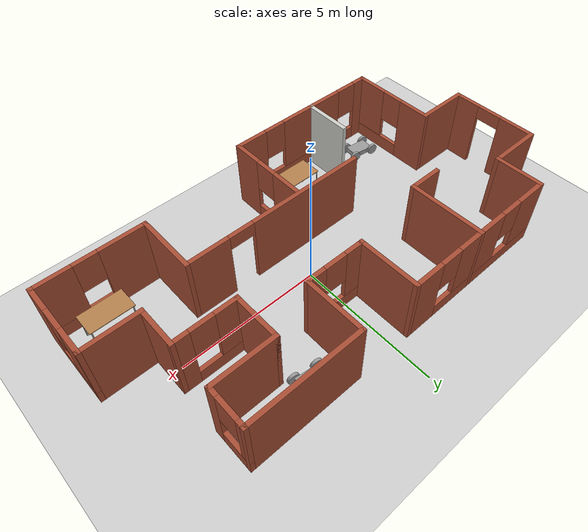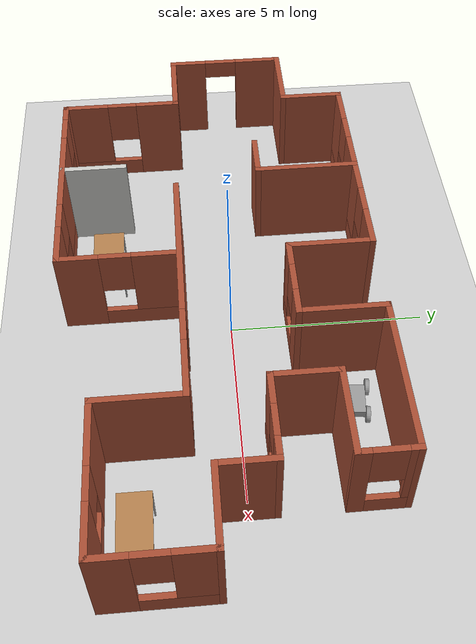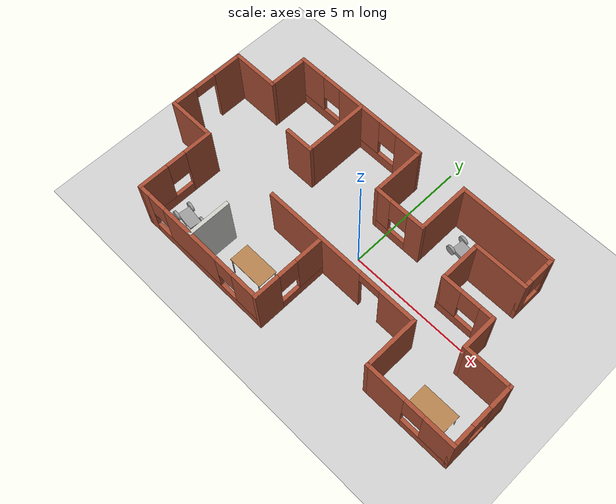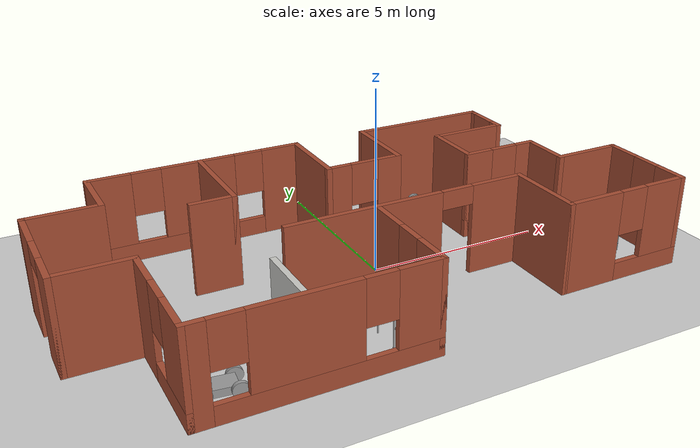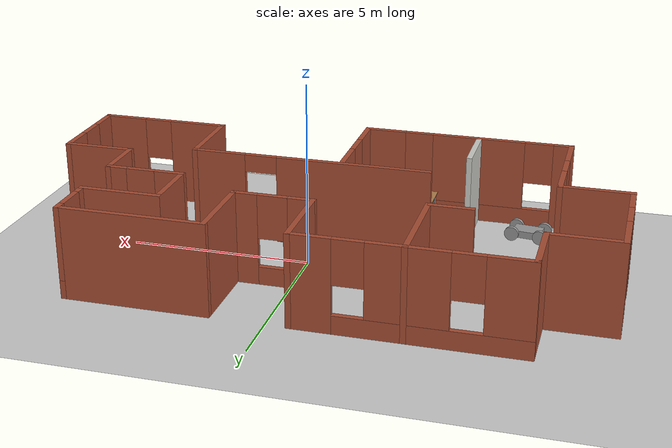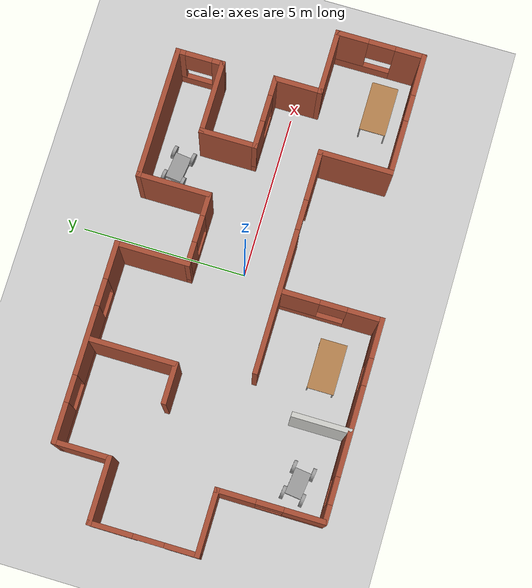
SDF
<sdf version="1.6">
 <world name="default">
  <light name="sun" type="directional">
   <pose>0 0 10 0 -0 0</pose>
   <diffuse>0.8 0.8 0.8 1</diffuse>
   <specular>0.2 0.2 0.2 1</specular>
   <attenuation>
    <range>1000</range>
    <constant>0.9</constant>
    <linear>0.01</linear>
    <quadratic>0.001</quadratic>
   </attenuation>
   <direction>-0.5 0.1 -0.9</direction>
  </light>
  <model name="ground_plane">
   <static>1</static>
   <link name="link">
    <collision name="collision">
     <geometry><plane><normal>0 0 1</normal><size>100 100</size></plane></geometry>
     <surface><friction><ode><mu>100</mu><mu2>50</mu2></ode></friction></surface>
    </collision>
    <visual name="visual">
     <cast_shadows>0</cast_shadows>
     <geometry><plane><normal>0 0 1</normal><size>100 100</size></plane></geometry>
     <material>
      <script><uri>file://media/materials/scripts/gazebo.material</uri><name>Gazebo/Grey</name></script>
     </material>
    </visual>
   </link>
  </model>
  <gravity>0 0 -9.8</gravity>
  <magnetic_field>6e-06 2.3e-05 -4.2e-05</magnetic_field>
  <atmosphere type="adiabatic"/>
  <physics name="default_physics" default="0" type="ode">
   <max_step_size>0.001</max_step_size>
   <real_time_factor>1</real_time_factor>
   <real_time_update_rate>1000</real_time_update_rate>
  </physics>
  <scene><ambient>0.4 0.4 0.4 1</ambient><background>0.7 0.7 0.7 1</background><shadows>1</shadows></scene>
  <spherical_coordinates>
   <surface_model>EARTH_WGS84</surface_model>
   <latitude_deg>0</latitude_deg>
   <longitude_deg>0</longitude_deg>
   <elevation>0</elevation>
   <heading_deg>0</heading_deg>
  </spherical_coordinates>
  <model name="building">
   <pose>-0.550552 -0.291737 0 0 -0 0</pose>
   <link name="Wall_1">
    <pose>0.85 -0.900213 0 0 -0 0</pose>
    <visual name="Wall_1_Visual_0">
     <pose>-1.22383 0 1.25 0 -0 0</pose>
     <geometry><box><size>4.30235 0.15 2.5</size></box></geometry>
     <material>
      <script><uri>file://media/materials/scripts/gazebo.material</uri><name>Gazebo/Bricks</name></script>
      <ambient>0.996078 0.47451 0.0196078 1</ambient>
     </material>
     <meta><layer>0</layer></meta>
    </visual>
    <collision name="Wall_1_Collision_0">
     <geometry><box><size>4.30235 0.15 2.5</size></box></geometry>
     <pose>-1.22383 0 1.25 0 -0 0</pose>
    </collision>
    <visual name="Wall_1_Visual_1">
     <pose>2.60117 0 1.25 0 -0 0</pose>
     <geometry><box><size>1.54765 0.15 2.5</size></box></geometry>
     <material>
      <script><uri>file://media/materials/scripts/gazebo.material</uri><name>Gazebo/Bricks</name></script>
      <ambient>0.996078 0.47451 0.0196078 1</ambient>
     </material>
     <meta><layer>0</layer></meta>
    </visual>
    <collision name="Wall_1_Collision_1">
     <geometry><box><size>1.54765 0.15 2.5</size></box></geometry>
     <pose>2.60117 0 1.25 0 -0 0</pose>
    </collision>
    <visual name="Wall_1_Visual_2">
     <pose>1.37735 0 2.25 0 -0 0</pose>
     <geometry><box><size>0.9 0.15 0.5</size></box></geometry>
     <material>
      <script><uri>file://media/materials/scripts/gazebo.material</uri><name>Gazebo/Bricks</name></script>
      <ambient>0.996078 0.47451 0.0196078 1</ambient>
     </material>
     <meta><layer>0</layer></meta>
    </visual>
    <collision name="Wall_1_Collision_2">
     <geometry><box><size>0.9 0.15 0.5</size></box></geometry>
     <pose>1.37735 0 2.25 0 -0 0</pose>
    </collision>
   </link>
   <link name="Wall_10">
    <pose>5.9 3.22479 0 0 -0 1.5708</pose>
    <visual name="Wall_10_Visual_0">
     <pose>-0.55649 0 1.25 0 -0 0</pose>
     <geometry><box><size>0.38702 0.15 2.5</size></box></geometry>
     <material>
      <script><uri>file://media/materials/scripts/gazebo.material</uri><name>Gazebo/Bricks</name></script>
      <ambient>0.996078 0.47451 0.0196078 1</ambient>
     </material>
     <meta><layer>0</layer></meta>
    </visual>
    <collision name="Wall_10_Collision_0">
     <geometry><box><size>0.38702 0.15 2.5</size></box></geometry>
     <pose>-0.55649 0 1.25 0 -0 0</pose>
    </collision>
    <visual name="Wall_10_Visual_1">
     <pose>0.19351 0 0.25 0 -0 0</pose>
     <geometry><box><size>1.11298 0.15 0.5</size></box></geometry>
     <material>
      <script><uri>file://media/materials/scripts/gazebo.material</uri><name>Gazebo/Bricks</name></script>
      <ambient>0.996078 0.47451 0.0196078 1</ambient>
     </material>
     <meta><layer>0</layer></meta>
    </visual>
    <collision name="Wall_10_Collision_1">
     <geometry><box><size>1.11298 0.15 0.5</size></box></geometry>
     <pose>0.19351 0 0.25 0 -0 0</pose>
    </collision>
    <visual name="Wall_10_Visual_2">
     <pose>0.59351 0 1.5 0 -0 0</pose>
     <geometry><box><size>0.31298 0.15 2</size></box></geometry>
     <material>
      <script><uri>file://media/materials/scripts/gazebo.material</uri><name>Gazebo/Bricks</name></script>
      <ambient>0.996078 0.47451 0.0196078 1</ambient>
     </material>
     <meta><layer>0</layer></meta>
    </visual>
    <collision name="Wall_10_Collision_2">
     <geometry><box><size>0.31298 0.15 2</size></box></geometry>
     <pose>0.59351 0 1.5 0 -0 0</pose>
    </collision>
    <visual name="Wall_10_Visual_3">
     <pose>0.03702 0 1.9 0 -0 0</pose>
     <geometry><box><size>0.8 0.15 1.2</size></box></geometry>
     <material>
      <script><uri>file://media/materials/scripts/gazebo.material</uri><name>Gazebo/Bricks</name></script>
      <ambient>0.996078 0.47451 0.0196078 1</ambient>
     </material>
     <meta><layer>0</layer></meta>
    </visual>
    <collision name="Wall_10_Collision_3">
     <geometry><box><size>0.8 0.15 1.2</size></box></geometry>
     <pose>0.03702 0 1.9 0 -0 0</pose>
    </collision>
   </link>
   <link name="Wall_11">
    <collision name="Wall_11_Collision">
     <geometry><box><size>4 0.15 2.5</size></box></geometry>
     <pose>0 0 1.25 0 -0 0</pose>
    </collision>
    <visual name="Wall_11_Visual">
     <pose>0 0 1.25 0 -0 0</pose>
     <geometry><box><size>4 0.15 2.5</size></box></geometry>
     <material>
      <script><uri>file://media/materials/scripts/gazebo.material</uri><name>Gazebo/Bricks</name></script>
      <ambient>0.996078 0.47451 0.0196078 1</ambient>
     </material>
     <meta><layer>0</layer></meta>
    </visual>
    <pose>3.975 3.89979 0 0 -0 3.14159</pose>
   </link>
   <link name="Wall_12">
    <collision name="Wall_12_Collision">
     <geometry><box><size>2.25 0.15 2.5</size></box></geometry>
     <pose>0 0 1.25 0 -0 0</pose>
    </collision>
    <visual name="Wall_12_Visual">
     <pose>0 0 1.25 0 -0 0</pose>
     <geometry><box><size>2.25 0.15 2.5</size></box></geometry>
     <material>
      <script><uri>file://media/materials/scripts/gazebo.material</uri><name>Gazebo/Bricks</name></script>
      <ambient>0.996078 0.47451 0.0196078 1</ambient>
     </material>
     <meta><layer>0</layer></meta>
    </visual>
    <pose>2.05 2.84979 0 0 0 -1.5708</pose>
   </link>
   <link name="Wall_13">
    <pose>1 1.79979 0 0 -0 3.14159</pose>
    <visual name="Wall_13_Visual_0">
     <pose>-0.76437 0 1.25 0 -0 0</pose>
     <geometry><box><size>0.72126 0.15 2.5</size></box></geometry>
     <material>
      <script><uri>file://media/materials/scripts/gazebo.material</uri><name>Gazebo/Bricks</name></script>
      <ambient>0.996078 0.47451 0.0196078 1</ambient>
     </material>
     <meta><layer>0</layer></meta>
    </visual>
    <collision name="Wall_13_Collision_0">
     <geometry><box><size>0.72126 0.15 2.5</size></box></geometry>
     <pose>-0.76437 0 1.25 0 -0 0</pose>
    </collision>
    <visual name="Wall_13_Visual_1">
     <pose>0.36063 0 0.25 0 -0 0</pose>
     <geometry><box><size>1.52874 0.15 0.5</size></box></geometry>
     <material>
      <script><uri>file://media/materials/scripts/gazebo.material</uri><name>Gazebo/Bricks</name></script>
      <ambient>0.996078 0.47451 0.0196078 1</ambient>
     </material>
     <meta><layer>0</layer></meta>
    </visual>
    <collision name="Wall_13_Collision_1">
     <geometry><box><size>1.52874 0.15 0.5</size></box></geometry>
     <pose>0.36063 0 0.25 0 -0 0</pose>
    </collision>
    <visual name="Wall_13_Visual_2">
     <pose>0.76063 0 1.5 0 -0 0</pose>
     <geometry><box><size>0.72874 0.15 2</size></box></geometry>
     <material>
      <script><uri>file://media/materials/scripts/gazebo.material</uri><name>Gazebo/Bricks</name></script>
      <ambient>0.996078 0.47451 0.0196078 1</ambient>
     </material>
     <meta><layer>0</layer></meta>
    </visual>
    <collision name="Wall_13_Collision_2">
     <geometry><box><size>0.72874 0.15 2</size></box></geometry>
     <pose>0.76063 0 1.5 0 -0 0</pose>
    </collision>
    <visual name="Wall_13_Visual_3">
     <pose>-0.00374 0 1.9 0 -0 0</pose>
     <geometry><box><size>0.8 0.15 1.2</size></box></geometry>
     <material>
      <script><uri>file://media/materials/scripts/gazebo.material</uri><name>Gazebo/Bricks</name></script>
      <ambient>0.996078 0.47451 0.0196078 1</ambient>
     </material>
     <meta><layer>0</layer></meta>
    </visual>
    <collision name="Wall_13_Collision_3">
     <geometry><box><size>0.8 0.15 1.2</size></box></geometry>
     <pose>-0.00374 0 1.9 0 -0 0</pose>
    </collision>
   </link>
   <link name="Wall_14">
    <collision name="Wall_14_Collision">
     <geometry><box><size>2.25 0.15 2.5</size></box></geometry>
     <pose>0 0 1.25 0 -0 0</pose>
    </collision>
    <visual name="Wall_14_Visual">
     <pose>0 0 1.25 0 -0 0</pose>
     <geometry><box><size>2.25 0.15 2.5</size></box></geometry>
     <material>
      <script><uri>file://media/materials/scripts/gazebo.material</uri><name>Gazebo/Bricks</name></script>
      <ambient>0.996078 0.47451 0.0196078 1</ambient>
     </material>
     <meta><layer>0</layer></meta>
    </visual>
    <pose>-0.05 2.84979 0 0 -0 1.5708</pose>
   </link>
   <link name="Wall_15">
    <pose>-2.975 3.89979 0 0 -0 3.14159</pose>
    <visual name="Wall_15_Visual_0">
     <pose>-2.42586 0 1.25 0 -0 0</pose>
     <geometry><box><size>1.14828 0.15 2.5</size></box></geometry>
     <material>
      <script><uri>file://media/materials/scripts/gazebo.material</uri><name>Gazebo/Bricks</name></script>
      <ambient>0.996078 0.47451 0.0196078 1</ambient>
     </material>
     <meta><layer>0</layer></meta>
    </visual>
    <collision name="Wall_15_Collision_0">
     <geometry><box><size>1.14828 0.15 2.5</size></box></geometry>
     <pose>-2.42586 0 1.25 0 -0 0</pose>
    </collision>
    <visual name="Wall_15_Visual_1">
     <pose>0.57414 0 0.25 0 -0 0</pose>
     <geometry><box><size>4.85172 0.15 0.5</size></box></geometry>
     <material>
      <script><uri>file://media/materials/scripts/gazebo.material</uri><name>Gazebo/Bricks</name></script>
      <ambient>0.996078 0.47451 0.0196078 1</ambient>
     </material>
     <meta><layer>0</layer></meta>
    </visual>
    <collision name="Wall_15_Collision_1">
     <geometry><box><size>4.85172 0.15 0.5</size></box></geometry>
     <pose>0.57414 0 0.25 0 -0 0</pose>
    </collision>
    <visual name="Wall_15_Visual_2">
     <pose>-0.02861 0 1.5 0 -0 0</pose>
     <geometry><box><size>2.04622 0.15 2</size></box></geometry>
     <material>
      <script><uri>file://media/materials/scripts/gazebo.material</uri><name>Gazebo/Bricks</name></script>
      <ambient>0.996078 0.47451 0.0196078 1</ambient>
     </material>
     <meta><layer>0</layer></meta>
    </visual>
    <collision name="Wall_15_Collision_2">
     <geometry><box><size>2.04622 0.15 2</size></box></geometry>
     <pose>-0.02861 0 1.5 0 -0 0</pose>
    </collision>
    <visual name="Wall_15_Visual_3">
     <pose>2.39725 0 1.5 0 -0 0</pose>
     <geometry><box><size>1.2055 0.15 2</size></box></geometry>
     <material>
      <script><uri>file://media/materials/scripts/gazebo.material</uri><name>Gazebo/Bricks</name></script>
      <ambient>0.996078 0.47451 0.0196078 1</ambient>
     </material>
     <meta><layer>0</layer></meta>
    </visual>
    <collision name="Wall_15_Collision_3">
     <geometry><box><size>1.2055 0.15 2</size></box></geometry>
     <pose>2.39725 0 1.5 0 -0 0</pose>
    </collision>
    <visual name="Wall_15_Visual_4">
     <pose>-1.45172 0 1.9 0 -0 0</pose>
     <geometry><box><size>0.8 0.15 1.2</size></box></geometry>
     <material>
      <script><uri>file://media/materials/scripts/gazebo.material</uri><name>Gazebo/Bricks</name></script>
      <ambient>0.996078 0.47451 0.0196078 1</ambient>
     </material>
     <meta><layer>0</layer></meta>
    </visual>
    <collision name="Wall_15_Collision_4">
     <geometry><box><size>0.8 0.15 1.2</size></box></geometry>
     <pose>-1.45172 0 1.9 0 -0 0</pose>
    </collision>
    <visual name="Wall_15_Visual_5">
     <pose>1.3945 0 1.9 0 -0 0</pose>
     <geometry><box><size>0.8 0.15 1.2</size></box></geometry>
     <material>
      <script><uri>file://media/materials/scripts/gazebo.material</uri><name>Gazebo/Bricks</name></script>
      <ambient>0.996078 0.47451 0.0196078 1</ambient>
     </material>
     <meta><layer>0</layer></meta>
    </visual>
    <collision name="Wall_15_Collision_5">
     <geometry><box><size>0.8 0.15 1.2</size></box></geometry>
     <pose>1.3945 0 1.9 0 -0 0</pose>
    </collision>
   </link>
   <link name="Wall_16">
    <collision name="Wall_16_Collision">
     <geometry><box><size>1.75 0.15 2.5</size></box></geometry>
     <pose>0 0 1.25 0 -0 0</pose>
    </collision>
    <visual name="Wall_16_Visual">
     <pose>0 0 1.25 0 -0 0</pose>
     <geometry><box><size>1.75 0.15 2.5</size></box></geometry>
     <material>
      <script><uri>file://media/materials/scripts/gazebo.material</uri><name>Gazebo/Bricks</name></script>
      <ambient>0.996078 0.47451 0.0196078 1</ambient>
     </material>
     <meta><layer>0</layer></meta>
    </visual>
    <pose>-5.9 3.09979 0 0 0 -1.5708</pose>
   </link>
   <link name="Wall_17">
    <collision name="Wall_17_Collision">
     <geometry><box><size>2 0.15 2.5</size></box></geometry>
     <pose>0 0 1.25 0 -0 0</pose>
    </collision>
    <visual name="Wall_17_Visual">
     <pose>0 0 1.25 0 -0 0</pose>
     <geometry><box><size>2 0.15 2.5</size></box></geometry>
     <material>
      <script><uri>file://media/materials/scripts/gazebo.material</uri><name>Gazebo/Bricks</name></script>
      <ambient>0.996078 0.47451 0.0196078 1</ambient>
     </material>
     <meta><layer>0</layer></meta>
    </visual>
    <pose>-6.825 2.29979 0 0 -0 3.14159</pose>
   </link>
   <link name="Wall_18">
    <pose>-7.75 0.749787 0 0 0 -1.5708</pose>
    <visual name="Wall_18_Visual_0">
     <pose>-0.9635 0 1.25 0 -0 0</pose>
     <geometry><box><size>1.323 0.15 2.5</size></box></geometry>
     <material>
      <script><uri>file://media/materials/scripts/gazebo.material</uri><name>Gazebo/Bricks</name></script>
      <ambient>0.996078 0.47451 0.0196078 1</ambient>
     </material>
     <meta><layer>0</layer></meta>
    </visual>
    <collision name="Wall_18_Collision_0">
     <geometry><box><size>1.323 0.15 2.5</size></box></geometry>
     <pose>-0.9635 0 1.25 0 -0 0</pose>
    </collision>
    <visual name="Wall_18_Visual_1">
     <pose>1.1115 0 1.25 0 -0 0</pose>
     <geometry><box><size>1.027 0.15 2.5</size></box></geometry>
     <material>
      <script><uri>file://media/materials/scripts/gazebo.material</uri><name>Gazebo/Bricks</name></script>
      <ambient>0.996078 0.47451 0.0196078 1</ambient>
     </material>
     <meta><layer>0</layer></meta>
    </visual>
    <collision name="Wall_18_Collision_1">
     <geometry><box><size>1.027 0.15 2.5</size></box></geometry>
     <pose>1.1115 0 1.25 0 -0 0</pose>
    </collision>
    <visual name="Wall_18_Visual_2">
     <pose>0.147999 0 2.25 0 -0 0</pose>
     <geometry><box><size>0.9 0.15 0.5</size></box></geometry>
     <material>
      <script><uri>file://media/materials/scripts/gazebo.material</uri><name>Gazebo/Bricks</name></script>
      <ambient>0.996078 0.47451 0.0196078 1</ambient>
     </material>
     <meta><layer>0</layer></meta>
    </visual>
    <collision name="Wall_18_Collision_2">
     <geometry><box><size>0.9 0.15 0.5</size></box></geometry>
     <pose>0.147999 0 2.25 0 -0 0</pose>
    </collision>
   </link>
   <link name="Wall_19">
    <collision name="Wall_19_Collision">
     <geometry><box><size>2 0.15 2.5</size></box></geometry>
     <pose>0 0 1.25 0 -0 0</pose>
    </collision>
    <visual name="Wall_19_Visual">
     <pose>0 0 1.25 0 -0 0</pose>
     <geometry><box><size>2 0.15 2.5</size></box></geometry>
     <material>
      <script><uri>file://media/materials/scripts/gazebo.material</uri><name>Gazebo/Bricks</name></script>
      <ambient>0.996078 0.47451 0.0196078 1</ambient>
     </material>
     <meta><layer>0</layer></meta>
    </visual>
    <pose>-6.825 -0.800213 0 0 -0 0</pose>
   </link>
   <link name="Wall_2">
    <collision name="Wall_2_Collision">
     <geometry><box><size>2.25 0.15 2.5</size></box></geometry>
     <pose>0 0 1.25 0 -0 0</pose>
    </collision>
    <visual name="Wall_2_Visual">
     <pose>0 0 1.25 0 -0 0</pose>
     <geometry><box><size>2.25 0.15 2.5</size></box></geometry>
     <material>
      <script><uri>file://media/materials/scripts/gazebo.material</uri><name>Gazebo/Bricks</name></script>
      <ambient>0.996078 0.47451 0.0196078 1</ambient>
     </material>
     <meta><layer>0</layer></meta>
    </visual>
    <pose>4.15 -1.95021 0 0 0 -1.5708</pose>
   </link>
   <link name="Wall_20">
    <pose>-5.9 -2.35021 0 0 0 -1.5708</pose>
    <visual name="Wall_20_Visual_0">
     <pose>-1.02549 0 1.25 0 -0 0</pose>
     <geometry><box><size>1.19902 0.15 2.5</size></box></geometry>
     <material>
      <script><uri>file://media/materials/scripts/gazebo.material</uri><name>Gazebo/Bricks</name></script>
      <ambient>0.996078 0.47451 0.0196078 1</ambient>
     </material>
     <meta><layer>0</layer></meta>
    </visual>
    <collision name="Wall_20_Collision_0">
     <geometry><box><size>1.19902 0.15 2.5</size></box></geometry>
     <pose>-1.02549 0 1.25 0 -0 0</pose>
    </collision>
    <visual name="Wall_20_Visual_1">
     <pose>0.599511 0 0.25 0 -0 0</pose>
     <geometry><box><size>2.05098 0.15 0.5</size></box></geometry>
     <material>
      <script><uri>file://media/materials/scripts/gazebo.material</uri><name>Gazebo/Bricks</name></script>
      <ambient>0.996078 0.47451 0.0196078 1</ambient>
     </material>
     <meta><layer>0</layer></meta>
    </visual>
    <collision name="Wall_20_Collision_1">
     <geometry><box><size>2.05098 0.15 0.5</size></box></geometry>
     <pose>0.599511 0 0.25 0 -0 0</pose>
    </collision>
    <visual name="Wall_20_Visual_2">
     <pose>0.999511 0 1.5 0 -0 0</pose>
     <geometry><box><size>1.25098 0.15 2</size></box></geometry>
     <material>
      <script><uri>file://media/materials/scripts/gazebo.material</uri><name>Gazebo/Bricks</name></script>
      <ambient>0.996078 0.47451 0.0196078 1</ambient>
     </material>
     <meta><layer>0</layer></meta>
    </visual>
    <collision name="Wall_20_Collision_2">
     <geometry><box><size>1.25098 0.15 2</size></box></geometry>
     <pose>0.999511 0 1.5 0 -0 0</pose>
    </collision>
    <visual name="Wall_20_Visual_3">
     <pose>-0.025979 0 1.9 0 -0 0</pose>
     <geometry><box><size>0.8 0.15 1.2</size></box></geometry>
     <material>
      <script><uri>file://media/materials/scripts/gazebo.material</uri><name>Gazebo/Bricks</name></script>
      <ambient>0.996078 0.47451 0.0196078 1</ambient>
     </material>
     <meta><layer>0</layer></meta>
    </visual>
    <collision name="Wall_20_Collision_3">
     <geometry><box><size>0.8 0.15 1.2</size></box></geometry>
     <pose>-0.025979 0 1.9 0 -0 0</pose>
    </collision>
   </link>
   <link name="Wall_21">
    <pose>-2.975 -3.90021 0 0 -0 0</pose>
    <visual name="Wall_21_Visual_0">
     <pose>-2.71645 0 1.25 0 -0 0</pose>
     <geometry><box><size>0.567095 0.15 2.5</size></box></geometry>
     <material>
      <script><uri>file://media/materials/scripts/gazebo.material</uri><name>Gazebo/Bricks</name></script>
      <ambient>0.996078 0.47451 0.0196078 1</ambient>
     </material>
     <meta><layer>0</layer></meta>
    </visual>
    <collision name="Wall_21_Collision_0">
     <geometry><box><size>0.567095 0.15 2.5</size></box></geometry>
     <pose>-2.71645 0 1.25 0 -0 0</pose>
    </collision>
    <visual name="Wall_21_Visual_1">
     <pose>0.283547 0 0.25 0 -0 0</pose>
     <geometry><box><size>5.4329 0.15 0.5</size></box></geometry>
     <material>
      <script><uri>file://media/materials/scripts/gazebo.material</uri><name>Gazebo/Bricks</name></script>
      <ambient>0.996078 0.47451 0.0196078 1</ambient>
     </material>
     <meta><layer>0</layer></meta>
    </visual>
    <collision name="Wall_21_Collision_1">
     <geometry><box><size>5.4329 0.15 0.5</size></box></geometry>
     <pose>0.283547 0 0.25 0 -0 0</pose>
    </collision>
    <visual name="Wall_21_Visual_2">
     <pose>-0.317192 0 1.5 0 -0 0</pose>
     <geometry><box><size>2.63143 0.15 2</size></box></geometry>
     <material>
      <script><uri>file://media/materials/scripts/gazebo.material</uri><name>Gazebo/Bricks</name></script>
      <ambient>0.996078 0.47451 0.0196078 1</ambient>
     </material>
     <meta><layer>0</layer></meta>
    </visual>
    <collision name="Wall_21_Collision_2">
     <geometry><box><size>2.63143 0.15 2</size></box></geometry>
     <pose>-0.317192 0 1.5 0 -0 0</pose>
    </collision>
    <visual name="Wall_21_Visual_3">
     <pose>2.39926 0 1.5 0 -0 0</pose>
     <geometry><box><size>1.20148 0.15 2</size></box></geometry>
     <material>
      <script><uri>file://media/materials/scripts/gazebo.material</uri><name>Gazebo/Bricks</name></script>
      <ambient>0.996078 0.47451 0.0196078 1</ambient>
     </material>
     <meta><layer>0</layer></meta>
    </visual>
    <collision name="Wall_21_Collision_3">
     <geometry><box><size>1.20148 0.15 2</size></box></geometry>
     <pose>2.39926 0 1.5 0 -0 0</pose>
    </collision>
    <visual name="Wall_21_Visual_4">
     <pose>-2.0329 0 1.9 0 -0 0</pose>
     <geometry><box><size>0.8 0.15 1.2</size></box></geometry>
     <material>
      <script><uri>file://media/materials/scripts/gazebo.material</uri><name>Gazebo/Bricks</name></script>
      <ambient>0.996078 0.47451 0.0196078 1</ambient>
     </material>
     <meta><layer>0</layer></meta>
    </visual>
    <collision name="Wall_21_Collision_4">
     <geometry><box><size>0.8 0.15 1.2</size></box></geometry>
     <pose>-2.0329 0 1.9 0 -0 0</pose>
    </collision>
    <visual name="Wall_21_Visual_5">
     <pose>1.39852 0 1.9 0 -0 0</pose>
     <geometry><box><size>0.8 0.15 1.2</size></box></geometry>
     <material>
      <script><uri>file://media/materials/scripts/gazebo.material</uri><name>Gazebo/Bricks</name></script>
      <ambient>0.996078 0.47451 0.0196078 1</ambient>
     </material>
     <meta><layer>0</layer></meta>
    </visual>
    <collision name="Wall_21_Collision_5">
     <geometry><box><size>0.8 0.15 1.2</size></box></geometry>
     <pose>1.39852 0 1.9 0 -0 0</pose>
    </collision>
   </link>
   <link name="Wall_22">
    <pose>-0.05 -2.47521 0 0 -0 1.5708</pose>
    <visual name="Wall_22_Visual_0">
     <pose>-0.954311 0 1.25 0 -0 0</pose>
     <geometry><box><size>1.09138 0.15 2.5</size></box></geometry>
     <material>
      <script><uri>file://media/materials/scripts/gazebo.material</uri><name>Gazebo/Bricks</name></script>
      <ambient>0.996078 0.47451 0.0196078 1</ambient>
     </material>
     <meta><layer>0</layer></meta>
    </visual>
    <collision name="Wall_22_Collision_0">
     <geometry><box><size>1.09138 0.15 2.5</size></box></geometry>
     <pose>-0.954311 0 1.25 0 -0 0</pose>
    </collision>
    <visual name="Wall_22_Visual_1">
     <pose>0.545689 0 0.25 0 -0 0</pose>
     <geometry><box><size>1.90862 0.15 0.5</size></box></geometry>
     <material>
      <script><uri>file://media/materials/scripts/gazebo.material</uri><name>Gazebo/Bricks</name></script>
      <ambient>0.996078 0.47451 0.0196078 1</ambient>
     </material>
     <meta><layer>0</layer></meta>
    </visual>
    <collision name="Wall_22_Collision_1">
     <geometry><box><size>1.90862 0.15 0.5</size></box></geometry>
     <pose>0.545689 0 0.25 0 -0 0</pose>
    </collision>
    <visual name="Wall_22_Visual_2">
     <pose>0.945689 0 1.5 0 -0 0</pose>
     <geometry><box><size>1.10862 0.15 2</size></box></geometry>
     <material>
      <script><uri>file://media/materials/scripts/gazebo.material</uri><name>Gazebo/Bricks</name></script>
      <ambient>0.996078 0.47451 0.0196078 1</ambient>
     </material>
     <meta><layer>0</layer></meta>
    </visual>
    <collision name="Wall_22_Collision_2">
     <geometry><box><size>1.10862 0.15 2</size></box></geometry>
     <pose>0.945689 0 1.5 0 -0 0</pose>
    </collision>
    <visual name="Wall_22_Visual_3">
     <pose>-0.008622 0 1.9 0 -0 0</pose>
     <geometry><box><size>0.8 0.15 1.2</size></box></geometry>
     <material>
      <script><uri>file://media/materials/scripts/gazebo.material</uri><name>Gazebo/Bricks</name></script>
      <ambient>0.996078 0.47451 0.0196078 1</ambient>
     </material>
     <meta><layer>0</layer></meta>
    </visual>
    <collision name="Wall_22_Collision_3">
     <geometry><box><size>0.8 0.15 1.2</size></box></geometry>
     <pose>-0.008622 0 1.9 0 -0 0</pose>
    </collision>
   </link>
   <link name="Wall_25">
    <collision name="Wall_25_Collision">
     <geometry><box><size>2.75 0.15 2.5</size></box></geometry>
     <pose>0 0 1.25 0 -0 0</pose>
    </collision>
    <visual name="Wall_25_Visual">
     <pose>0 0 1.25 0 -0 0</pose>
     <geometry><box><size>2.75 0.15 2.5</size></box></geometry>
     <material>
      <script><uri>file://media/materials/scripts/gazebo.material</uri><name>Gazebo/Bricks</name></script>
      <ambient>0.996078 0.47451 0.0196078 1</ambient>
     </material>
     <meta><layer>0</layer></meta>
    </visual>
    <pose>-2.87989 2.60021 0 0 0 -1.5708</pose>
   </link>
   <link name="Wall_26">
    <collision name="Wall_26_Collision">
     <geometry><box><size>1.25 0.15 2.5</size></box></geometry>
     <pose>0 0 1.25 0 -0 0</pose>
    </collision>
    <visual name="Wall_26_Visual">
     <pose>0 0 1.25 0 -0 0</pose>
     <geometry><box><size>1.25 0.15 2.5</size></box></geometry>
     <material>
      <script><uri>file://media/materials/scripts/gazebo.material</uri><name>Gazebo/Bricks</name></script>
      <ambient>0.996078 0.47451 0.0196078 1</ambient>
     </material>
     <meta><layer>0</layer></meta>
    </visual>
    <pose>-3.42989 1.30021 0 0 -0 3.14159</pose>
   </link>
   <link name="Wall_28">
    <collision name="Wall_28_Collision">
     <geometry><box><size>1.75 0.15 2.5</size></box></geometry>
     <pose>0 0 1.25 0 -0 0</pose>
    </collision>
    <visual name="Wall_28_Visual">
     <pose>0 0 1.25 0 -0 0</pose>
     <geometry><box><size>1.75 0.15 2.5</size></box></geometry>
     <material>
      <script><uri>file://media/materials/scripts/gazebo.material</uri><name>Gazebo/CeilingTiled</name></script>
      <ambient>1 0.764706 0.305882 1</ambient>
     </material>
     <meta><layer>0</layer></meta>
    </visual>
    <pose>-3.30549 -3.06704 0 0 -0 1.5708</pose>
   </link>
   <link name="Wall_3">
    <pose>5.95 -3.00021 0 0 -0 0</pose>
    <visual name="Wall_3_Visual_0">
     <pose>-1.04371 0 1.25 0 -0 0</pose>
     <geometry><box><size>1.66258 0.15 2.5</size></box></geometry>
     <material>
      <script><uri>file://media/materials/scripts/gazebo.material</uri><name>Gazebo/Bricks</name></script>
      <ambient>0.996078 0.47451 0.0196078 1</ambient>
     </material>
     <meta><layer>0</layer></meta>
    </visual>
    <collision name="Wall_3_Collision_0">
     <geometry><box><size>1.66258 0.15 2.5</size></box></geometry>
     <pose>-1.04371 0 1.25 0 -0 0</pose>
    </collision>
    <visual name="Wall_3_Visual_1">
     <pose>0.831289 0 0.25 0 -0 0</pose>
     <geometry><box><size>2.08742 0.15 0.5</size></box></geometry>
     <material>
      <script><uri>file://media/materials/scripts/gazebo.material</uri><name>Gazebo/Bricks</name></script>
      <ambient>0.996078 0.47451 0.0196078 1</ambient>
     </material>
     <meta><layer>0</layer></meta>
    </visual>
    <collision name="Wall_3_Collision_1">
     <geometry><box><size>2.08742 0.15 0.5</size></box></geometry>
     <pose>0.831289 0 0.25 0 -0 0</pose>
    </collision>
    <visual name="Wall_3_Visual_2">
     <pose>1.23129 0 1.5 0 -0 0</pose>
     <geometry><box><size>1.28742 0.15 2</size></box></geometry>
     <material>
      <script><uri>file://media/materials/scripts/gazebo.material</uri><name>Gazebo/Bricks</name></script>
      <ambient>0.996078 0.47451 0.0196078 1</ambient>
     </material>
     <meta><layer>0</layer></meta>
    </visual>
    <collision name="Wall_3_Collision_2">
     <geometry><box><size>1.28742 0.15 2</size></box></geometry>
     <pose>1.23129 0 1.5 0 -0 0</pose>
    </collision>
    <visual name="Wall_3_Visual_3">
     <pose>0.187578 0 1.9 0 -0 0</pose>
     <geometry><box><size>0.8 0.15 1.2</size></box></geometry>
     <material>
      <script><uri>file://media/materials/scripts/gazebo.material</uri><name>Gazebo/Bricks</name></script>
      <ambient>0.996078 0.47451 0.0196078 1</ambient>
     </material>
     <meta><layer>0</layer></meta>
    </visual>
    <collision name="Wall_3_Collision_3">
     <geometry><box><size>0.8 0.15 1.2</size></box></geometry>
     <pose>0.187578 0 1.9 0 -0 0</pose>
    </collision>
   </link>
   <link name="Wall_4">
    <pose>7.75 -1.70021 0 0 -0 1.5708</pose>
    <visual name="Wall_4_Visual_0">
     <pose>-0.906908 0 1.25 0 -0 0</pose>
     <geometry><box><size>0.936183 0.15 2.5</size></box></geometry>
     <material>
      <script><uri>file://media/materials/scripts/gazebo.material</uri><name>Gazebo/Bricks</name></script>
      <ambient>0.996078 0.47451 0.0196078 1</ambient>
     </material>
     <meta><layer>0</layer></meta>
    </visual>
    <collision name="Wall_4_Collision_0">
     <geometry><box><size>0.936183 0.15 2.5</size></box></geometry>
     <pose>-0.906908 0 1.25 0 -0 0</pose>
    </collision>
    <visual name="Wall_4_Visual_1">
     <pose>0.468092 0 0.25 0 -0 0</pose>
     <geometry><box><size>1.81382 0.15 0.5</size></box></geometry>
     <material>
      <script><uri>file://media/materials/scripts/gazebo.material</uri><name>Gazebo/Bricks</name></script>
      <ambient>0.996078 0.47451 0.0196078 1</ambient>
     </material>
     <meta><layer>0</layer></meta>
    </visual>
    <collision name="Wall_4_Collision_1">
     <geometry><box><size>1.81382 0.15 0.5</size></box></geometry>
     <pose>0.468092 0 0.25 0 -0 0</pose>
    </collision>
    <visual name="Wall_4_Visual_2">
     <pose>0.868092 0 1.5 0 -0 0</pose>
     <geometry><box><size>1.01382 0.15 2</size></box></geometry>
     <material>
      <script><uri>file://media/materials/scripts/gazebo.material</uri><name>Gazebo/Bricks</name></script>
      <ambient>0.996078 0.47451 0.0196078 1</ambient>
     </material>
     <meta><layer>0</layer></meta>
    </visual>
    <collision name="Wall_4_Collision_2">
     <geometry><box><size>1.01382 0.15 2</size></box></geometry>
     <pose>0.868092 0 1.5 0 -0 0</pose>
    </collision>
    <visual name="Wall_4_Visual_3">
     <pose>-0.038817 0 1.9 0 -0 0</pose>
     <geometry><box><size>0.8 0.15 1.2</size></box></geometry>
     <material>
      <script><uri>file://media/materials/scripts/gazebo.material</uri><name>Gazebo/Bricks</name></script>
      <ambient>0.996078 0.47451 0.0196078 1</ambient>
     </material>
     <meta><layer>0</layer></meta>
    </visual>
    <collision name="Wall_4_Collision_3">
     <geometry><box><size>0.8 0.15 1.2</size></box></geometry>
     <pose>-0.038817 0 1.9 0 -0 0</pose>
    </collision>
   </link>
   <link name="Wall_5">
    <collision name="Wall_5_Collision">
     <geometry><box><size>2 0.15 2.5</size></box></geometry>
     <pose>0 0 1.25 0 -0 0</pose>
    </collision>
    <visual name="Wall_5_Visual">
     <pose>0 0 1.25 0 -0 0</pose>
     <geometry><box><size>2 0.15 2.5</size></box></geometry>
     <material>
      <script><uri>file://media/materials/scripts/gazebo.material</uri><name>Gazebo/Bricks</name></script>
      <ambient>0.996078 0.47451 0.0196078 1</ambient>
     </material>
     <meta><layer>0</layer></meta>
    </visual>
    <pose>6.825 -0.400213 0 0 -0 3.14159</pose>
   </link>
   <link name="Wall_6">
    <collision name="Wall_6_Collision">
     <geometry><box><size>1.5 0.15 2.5</size></box></geometry>
     <pose>0 0 1.25 0 -0 0</pose>
    </collision>
    <visual name="Wall_6_Visual">
     <pose>0 0 1.25 0 -0 0</pose>
     <geometry><box><size>1.5 0.15 2.5</size></box></geometry>
     <material>
      <script><uri>file://media/materials/scripts/gazebo.material</uri><name>Gazebo/Bricks</name></script>
      <ambient>0.996078 0.47451 0.0196078 1</ambient>
     </material>
     <meta><layer>0</layer></meta>
    </visual>
    <pose>5.9 0.274787 0 0 -0 1.5708</pose>
   </link>
   <link name="Wall_7">
    <pose>4.85 0.949787 0 0 -0 3.14159</pose>
    <visual name="Wall_7_Visual_0">
     <pose>-0.821085 0 1.25 0 -0 0</pose>
     <geometry><box><size>0.607831 0.15 2.5</size></box></geometry>
     <material>
      <script><uri>file://media/materials/scripts/gazebo.material</uri><name>Gazebo/Bricks</name></script>
      <ambient>0.996078 0.47451 0.0196078 1</ambient>
     </material>
     <meta><layer>0</layer></meta>
    </visual>
    <collision name="Wall_7_Collision_0">
     <geometry><box><size>0.607831 0.15 2.5</size></box></geometry>
     <pose>-0.821085 0 1.25 0 -0 0</pose>
    </collision>
    <visual name="Wall_7_Visual_1">
     <pose>0.303915 0 0.25 0 -0 0</pose>
     <geometry><box><size>1.64217 0.15 0.5</size></box></geometry>
     <material>
      <script><uri>file://media/materials/scripts/gazebo.material</uri><name>Gazebo/Bricks</name></script>
      <ambient>0.996078 0.47451 0.0196078 1</ambient>
     </material>
     <meta><layer>0</layer></meta>
    </visual>
    <collision name="Wall_7_Collision_1">
     <geometry><box><size>1.64217 0.15 0.5</size></box></geometry>
     <pose>0.303915 0 0.25 0 -0 0</pose>
    </collision>
    <visual name="Wall_7_Visual_2">
     <pose>0.703915 0 1.5 0 -0 0</pose>
     <geometry><box><size>0.842169 0.15 2</size></box></geometry>
     <material>
      <script><uri>file://media/materials/scripts/gazebo.material</uri><name>Gazebo/Bricks</name></script>
      <ambient>0.996078 0.47451 0.0196078 1</ambient>
     </material>
     <meta><layer>0</layer></meta>
    </visual>
    <collision name="Wall_7_Collision_2">
     <geometry><box><size>0.842169 0.15 2</size></box></geometry>
     <pose>0.703915 0 1.5 0 -0 0</pose>
    </collision>
    <visual name="Wall_7_Visual_3">
     <pose>-0.117169 0 1.9 0 -0 0</pose>
     <geometry><box><size>0.8 0.15 1.2</size></box></geometry>
     <material>
      <script><uri>file://media/materials/scripts/gazebo.material</uri><name>Gazebo/Bricks</name></script>
      <ambient>0.996078 0.47451 0.0196078 1</ambient>
     </material>
     <meta><layer>0</layer></meta>
    </visual>
    <collision name="Wall_7_Collision_3">
     <geometry><box><size>0.8 0.15 1.2</size></box></geometry>
     <pose>-0.117169 0 1.9 0 -0 0</pose>
    </collision>
   </link>
   <link name="Wall_8">
    <collision name="Wall_8_Collision">
     <geometry><box><size>1.75 0.15 2.5</size></box></geometry>
     <pose>0 0 1.25 0 -0 0</pose>
    </collision>
    <visual name="Wall_8_Visual">
     <pose>0 0 1.25 0 -0 0</pose>
     <geometry><box><size>1.75 0.15 2.5</size></box></geometry>
     <material>
      <script><uri>file://media/materials/scripts/gazebo.material</uri><name>Gazebo/Bricks</name></script>
      <ambient>0.996078 0.47451 0.0196078 1</ambient>
     </material>
     <meta><layer>0</layer></meta>
    </visual>
    <pose>3.8 1.74979 0 0 -0 1.5708</pose>
   </link>
   <link name="Wall_9">
    <collision name="Wall_9_Collision">
     <geometry><box><size>2.25 0.15 2.5</size></box></geometry>
     <pose>0 0 1.25 0 -0 0</pose>
    </collision>
    <visual name="Wall_9_Visual">
     <pose>0 0 1.25 0 -0 0</pose>
     <geometry><box><size>2.25 0.15 2.5</size></box></geometry>
     <material>
      <script><uri>file://media/materials/scripts/gazebo.material</uri><name>Gazebo/Bricks</name></script>
      <ambient>0.996078 0.47451 0.0196078 1</ambient>
     </material>
     <meta><layer>0</layer></meta>
    </visual>
    <pose>4.85 2.54979 0 0 -0 0</pose>
   </link>
   <static>1</static>
  </model>
  <model name="robot">
   <link name="link_0">
    <pose>0 -0 -0.015999 0 -0 0</pose>
    <inertial>
     <mass>1</mass>
     <inertia>
      <ixx>0.166667</ixx>
      <ixy>0</ixy>
      <ixz>0</ixz>
      <iyy>0.166667</iyy>
      <iyz>0</iyz>
      <izz>0.166667</izz>
     </inertia>
    </inertial>
    <visual name="visual">
     <geometry><box><size>0.8 0.5 0.2</size></box></geometry>
     <material>
      <lighting>1</lighting>
      <script><uri>file://media/materials/scripts/gazebo.material</uri><name>Gazebo/Grey</name></script>
      <shader type="pixel"><normal_map>__default__</normal_map></shader>
      <ambient>0.3 0.3 0.3 1</ambient>
      <diffuse>0.7 0.7 0.7 1</diffuse>
      <specular>0.01 0.01 0.01 1</specular>
      <emissive>0 0 0 1</emissive>
     </material>
    </visual>
    <collision name="collision">
     <geometry><box><size>0.8 0.5 0.2</size></box></geometry>
     <surface>
      <friction>
       <ode><mu>1</mu><mu2>1</mu2><fdir1>0 0 0</fdir1><slip1>0</slip1><slip2>0</slip2></ode>
       <torsional>
        <coefficient>1</coefficient>
        <patch_radius>0</patch_radius>
        <surface_radius>0</surface_radius>
        <use_patch_radius>1</use_patch_radius>
        <ode><slip>0</slip></ode>
       </torsional>
      </friction>
      <bounce><restitution_coefficient>0</restitution_coefficient><threshold>1e+06</threshold></bounce>
      <contact>
       <collide_without_contact>0</collide_without_contact>
       <collide_without_contact_bitmask>1</collide_without_contact_bitmask>
       <collide_bitmask>1</collide_bitmask>
       <ode>
        <soft_cfm>0</soft_cfm>
        <soft_erp>0.2</soft_erp>
        <kp>1e+13</kp>
        <kd>1</kd>
        <max_vel>0.01</max_vel>
        <min_depth>0</min_depth>
       </ode>
       <bullet>
        <split_impulse>1</split_impulse>
        <split_impulse_penetration_threshold>-0.01</split_impulse_penetration_threshold>
        <soft_cfm>0</soft_cfm>
        <soft_erp>0.2</soft_erp>
        <kp>1e+13</kp>
        <kd>1</kd>
       </bullet>
      </contact>
     </surface>
    </collision>
   </link>
   <link name="link_1">
    <pose>-0.4 -0.300019 0.003997 1.5707 -0 0</pose>
    <inertial>
     <mass>1</mass>
     <inertia><ixx>0.145833</ixx><ixy>0</ixy><ixz>0</ixz><iyy>0.145833</iyy><iyz>0</iyz><izz>0.125</izz></inertia>
    </inertial>
    <visual name="visual">
     <geometry><cylinder><radius>0.2</radius><length>0.1</length></cylinder></geometry>
     <material>
      <lighting>1</lighting>
      <script><uri>file://media/materials/scripts/gazebo.material</uri><name>Gazebo/Grey</name></script>
      <shader type="pixel"><normal_map>__default__</normal_map></shader>
      <ambient>0.3 0.3 0.3 1</ambient>
      <diffuse>0.7 0.7 0.7 1</diffuse>
      <specular>0.01 0.01 0.01 1</specular>
      <emissive>0 0 0 1</emissive>
     </material>
    </visual>
    <collision name="collision">
     <geometry><cylinder><radius>0.2</radius><length>0.1</length></cylinder></geometry>
     <surface>
      <friction>
       <ode><mu>1</mu><mu2>1</mu2><fdir1>0 0 0</fdir1><slip1>0</slip1><slip2>0</slip2></ode>
       <torsional>
        <coefficient>1</coefficient>
        <patch_radius>0</patch_radius>
        <surface_radius>0</surface_radius>
        <use_patch_radius>1</use_patch_radius>
        <ode><slip>0</slip></ode>
       </torsional>
      </friction>
      <bounce><restitution_coefficient>0</restitution_coefficient><threshold>1e+06</threshold></bounce>
      <contact>
       <collide_without_contact>0</collide_without_contact>
       <collide_without_contact_bitmask>1</collide_without_contact_bitmask>
       <collide_bitmask>1</collide_bitmask>
       <ode>
        <soft_cfm>0</soft_cfm>
        <soft_erp>0.2</soft_erp>
        <kp>1e+13</kp>
        <kd>1</kd>
        <max_vel>0.01</max_vel>
        <min_depth>0</min_depth>
       </ode>
       <bullet>
        <split_impulse>1</split_impulse>
        <split_impulse_penetration_threshold>-0.01</split_impulse_penetration_threshold>
        <soft_cfm>0</soft_cfm>
        <soft_erp>0.2</soft_erp>
        <kp>1e+13</kp>
        <kd>1</kd>
       </bullet>
      </contact>
     </surface>
    </collision>
   </link>
   <link name="link_1_clone">
    <pose>0.4 -0.300019 0.004001 1.5707 -0 0</pose>
    <inertial>
     <mass>1</mass>
     <inertia><ixx>0.145833</ixx><ixy>0</ixy><ixz>0</ixz><iyy>0.145833</iyy><iyz>0</iyz><izz>0.125</izz></inertia>
    </inertial>
    <visual name="visual">
     <geometry><cylinder><radius>0.2</radius><length>0.1</length></cylinder></geometry>
     <material>
      <lighting>1</lighting>
      <script><uri>file://media/materials/scripts/gazebo.material</uri><name>Gazebo/Grey</name></script>
      <shader type="pixel"><normal_map>__default__</normal_map></shader>
      <ambient>0.3 0.3 0.3 1</ambient>
      <diffuse>0.7 0.7 0.7 1</diffuse>
      <specular>0.01 0.01 0.01 1</specular>
      <emissive>0 0 0 1</emissive>
     </material>
    </visual>
    <collision name="collision">
     <geometry><cylinder><radius>0.2</radius><length>0.1</length></cylinder></geometry>
     <surface>
      <friction>
       <ode><mu>1</mu><mu2>1</mu2><fdir1>0 0 0</fdir1><slip1>0</slip1><slip2>0</slip2></ode>
       <torsional>
        <coefficient>1</coefficient>
        <patch_radius>0</patch_radius>
        <surface_radius>0</surface_radius>
        <use_patch_radius>1</use_patch_radius>
        <ode><slip>0</slip></ode>
       </torsional>
      </friction>
      <bounce><restitution_coefficient>0</restitution_coefficient><threshold>1e+06</threshold></bounce>
      <contact>
       <collide_without_contact>0</collide_without_contact>
       <collide_without_contact_bitmask>1</collide_without_contact_bitmask>
       <collide_bitmask>1</collide_bitmask>
       <ode>
        <soft_cfm>0</soft_cfm>
        <soft_erp>0.2</soft_erp>
        <kp>1e+13</kp>
        <kd>1</kd>
        <max_vel>0.01</max_vel>
        <min_depth>0</min_depth>
       </ode>
       <bullet>
        <split_impulse>1</split_impulse>
        <split_impulse_penetration_threshold>-0.01</split_impulse_penetration_threshold>
        <soft_cfm>0</soft_cfm>
        <soft_erp>0.2</soft_erp>
        <kp>1e+13</kp>
        <kd>1</kd>
       </bullet>
      </contact>
     </surface>
    </collision>
   </link>
   <link name="link_1_clone_1">
    <pose>0.4 0.300019 0.004001 1.5707 -0 0</pose>
    <inertial>
     <mass>1</mass>
     <inertia><ixx>0.145833</ixx><ixy>0</ixy><ixz>0</ixz><iyy>0.145833</iyy><iyz>0</iyz><izz>0.125</izz></inertia>
    </inertial>
    <visual name="visual">
     <geometry><cylinder><radius>0.2</radius><length>0.1</length></cylinder></geometry>
     <material>
      <lighting>1</lighting>
      <script><uri>file://media/materials/scripts/gazebo.material</uri><name>Gazebo/Grey</name></script>
      <shader type="pixel"><normal_map>__default__</normal_map></shader>
      <ambient>0.3 0.3 0.3 1</ambient>
      <diffuse>0.7 0.7 0.7 1</diffuse>
      <specular>0.01 0.01 0.01 1</specular>
      <emissive>0 0 0 1</emissive>
     </material>
    </visual>
    <collision name="collision">
     <geometry><cylinder><radius>0.2</radius><length>0.1</length></cylinder></geometry>
     <surface>
      <friction>
       <ode><mu>1</mu><mu2>1</mu2><fdir1>0 0 0</fdir1><slip1>0</slip1><slip2>0</slip2></ode>
       <torsional>
        <coefficient>1</coefficient>
        <patch_radius>0</patch_radius>
        <surface_radius>0</surface_radius>
        <use_patch_radius>1</use_patch_radius>
        <ode><slip>0</slip></ode>
       </torsional>
      </friction>
      <bounce><restitution_coefficient>0</restitution_coefficient><threshold>1e+06</threshold></bounce>
      <contact>
       <collide_without_contact>0</collide_without_contact>
       <collide_without_contact_bitmask>1</collide_without_contact_bitmask>
       <collide_bitmask>1</collide_bitmask>
       <ode>
        <soft_cfm>0</soft_cfm>
        <soft_erp>0.2</soft_erp>
        <kp>1e+13</kp>
        <kd>1</kd>
        <max_vel>0.01</max_vel>
        <min_depth>0</min_depth>
       </ode>
       <bullet>
        <split_impulse>1</split_impulse>
        <split_impulse_penetration_threshold>-0.01</split_impulse_penetration_threshold>
        <soft_cfm>0</soft_cfm>
        <soft_erp>0.2</soft_erp>
        <kp>1e+13</kp>
        <kd>1</kd>
       </bullet>
      </contact>
     </surface>
    </collision>
   </link>
   <link name="link_1_clone_1_clone">
    <pose>-0.4 0.300019 0.004001 1.5707 -0 0</pose>
    <inertial>
     <mass>1</mass>
     <inertia><ixx>0.145833</ixx><ixy>0</ixy><ixz>0</ixz><iyy>0.145833</iyy><iyz>0</iyz><izz>0.125</izz></inertia>
    </inertial>
    <visual name="visual">
     <geometry><cylinder><radius>0.2</radius><length>0.1</length></cylinder></geometry>
     <material>
      <lighting>1</lighting>
      <script><uri>file://media/materials/scripts/gazebo.material</uri><name>Gazebo/Grey</name></script>
      <shader type="pixel"><normal_map>__default__</normal_map></shader>
      <ambient>0.3 0.3 0.3 1</ambient>
      <diffuse>0.7 0.7 0.7 1</diffuse>
      <specular>0.01 0.01 0.01 1</specular>
      <emissive>0 0 0 1</emissive>
     </material>
    </visual>
    <collision name="collision">
     <geometry><cylinder><radius>0.2</radius><length>0.1</length></cylinder></geometry>
     <surface>
      <friction>
       <ode><mu>1</mu><mu2>1</mu2><fdir1>0 0 0</fdir1><slip1>0</slip1><slip2>0</slip2></ode>
       <torsional>
        <coefficient>1</coefficient>
        <patch_radius>0</patch_radius>
        <surface_radius>0</surface_radius>
        <use_patch_radius>1</use_patch_radius>
        <ode><slip>0</slip></ode>
       </torsional>
      </friction>
      <bounce><restitution_coefficient>0</restitution_coefficient><threshold>1e+06</threshold></bounce>
      <contact>
       <collide_without_contact>0</collide_without_contact>
       <collide_without_contact_bitmask>1</collide_without_contact_bitmask>
       <collide_bitmask>1</collide_bitmask>
       <ode>
        <soft_cfm>0</soft_cfm>
        <soft_erp>0.2</soft_erp>
        <kp>1e+13</kp>
        <kd>1</kd>
        <max_vel>0.01</max_vel>
        <min_depth>0</min_depth>
       </ode>
       <bullet>
        <split_impulse>1</split_impulse>
        <split_impulse_penetration_threshold>-0.01</split_impulse_penetration_threshold>
        <soft_cfm>0</soft_cfm>
        <soft_erp>0.2</soft_erp>
        <kp>1e+13</kp>
        <kd>1</kd>
       </bullet>
      </contact>
     </surface>
    </collision>
   </link>
   <joint name="link_0_JOINT_0" type="revolute">
    <parent>link_0</parent>
    <child>link_1</child>
    <axis>
     <xyz>0 0 1</xyz>
     <use_parent_model_frame>0</use_parent_model_frame>
     <limit>
      <lower>-1.79769e+308</lower>
      <upper>1.79769e+308</upper>
      <effort>-1</effort>
      <velocity>-1</velocity>
     </limit>
     <dynamics>
      <spring_reference>0</spring_reference>
      <spring_stiffness>0</spring_stiffness>
      <damping>0</damping>
     </dynamics>
    </axis>
    <physics>
     <ode><limit><cfm>0</cfm><erp>0.2</erp></limit><suspension><cfm>0</cfm><erp>0.2</erp></suspension></ode>
    </physics>
   </joint>
   <joint name="link_0_JOINT_3" type="revolute">
    <parent>link_0</parent>
    <child>link_1_clone_1_clone</child>
    <axis>
     <xyz>0 0 1</xyz>
     <use_parent_model_frame>0</use_parent_model_frame>
     <limit>
      <lower>-1.79769e+308</lower>
      <upper>1.79769e+308</upper>
      <effort>-1</effort>
      <velocity>-1</velocity>
     </limit>
     <dynamics>
      <spring_reference>0</spring_reference>
      <spring_stiffness>0</spring_stiffness>
      <damping>0</damping>
     </dynamics>
    </axis>
    <physics>
     <ode><limit><cfm>0</cfm><erp>0.2</erp></limit><suspension><cfm>0</cfm><erp>0.2</erp></suspension></ode>
    </physics>
   </joint>
   <joint name="link_0_JOINT_5" type="revolute">
    <parent>link_0</parent>
    <child>link_1_clone_1</child>
    <axis>
     <xyz>0 0 1</xyz>
     <use_parent_model_frame>0</use_parent_model_frame>
     <limit>
      <lower>-1.79769e+308</lower>
      <upper>1.79769e+308</upper>
      <effort>-1</effort>
      <velocity>-1</velocity>
     </limit>
     <dynamics>
      <spring_reference>0</spring_reference>
      <spring_stiffness>0</spring_stiffness>
      <damping>0</damping>
     </dynamics>
    </axis>
    <physics>
     <ode><limit><cfm>0</cfm><erp>0.2</erp></limit><suspension><cfm>0</cfm><erp>0.2</erp></suspension></ode>
    </physics>
   </joint>
   <joint name="link_0_JOINT_6" type="revolute">
    <parent>link_0</parent>
    <child>link_1_clone</child>
    <axis>
     <xyz>0 0 1</xyz>
     <use_parent_model_frame>0</use_parent_model_frame>
     <limit>
      <lower>-1.79769e+308</lower>
      <upper>1.79769e+308</upper>
      <effort>-1</effort>
      <velocity>-1</velocity>
     </limit>
     <dynamics>
      <spring_reference>0</spring_reference>
      <spring_stiffness>0</spring_stiffness>
      <damping>0</damping>
     </dynamics>
    </axis>
    <physics>
     <ode><limit><cfm>0</cfm><erp>0.2</erp></limit><suspension><cfm>0</cfm><erp>0.2</erp></suspension></ode>
    </physics>
   </joint>
   <static>0</static>
   <pose>-5.49429 -3.23329 0.196004 0 0 -0.124515</pose>
  </model>
  <model name="robot_0">
   <link name="link_0">
    <pose>0 -0 -0.015999 0 -0 0</pose>
    <inertial>
     <mass>1</mass>
     <inertia>
      <ixx>0.166667</ixx>
      <ixy>0</ixy>
      <ixz>0</ixz>
      <iyy>0.166667</iyy>
      <iyz>0</iyz>
      <izz>0.166667</izz>
     </inertia>
    </inertial>
    <visual name="visual">
     <geometry><box><size>0.8 0.5 0.2</size></box></geometry>
     <material>
      <lighting>1</lighting>
      <script><uri>file://media/materials/scripts/gazebo.material</uri><name>Gazebo/Grey</name></script>
      <shader type="pixel"><normal_map>__default__</normal_map></shader>
      <ambient>0.3 0.3 0.3 1</ambient>
      <diffuse>0.7 0.7 0.7 1</diffuse>
      <specular>0.01 0.01 0.01 1</specular>
      <emissive>0 0 0 1</emissive>
     </material>
    </visual>
    <collision name="collision">
     <geometry><box><size>0.8 0.5 0.2</size></box></geometry>
     <surface>
      <friction>
       <ode><mu>1</mu><mu2>1</mu2><fdir1>0 0 0</fdir1><slip1>0</slip1><slip2>0</slip2></ode>
       <torsional>
        <coefficient>1</coefficient>
        <patch_radius>0</patch_radius>
        <surface_radius>0</surface_radius>
        <use_patch_radius>1</use_patch_radius>
        <ode><slip>0</slip></ode>
       </torsional>
      </friction>
      <bounce><restitution_coefficient>0</restitution_coefficient><threshold>1e+06</threshold></bounce>
      <contact>
       <collide_without_contact>0</collide_without_contact>
       <collide_without_contact_bitmask>1</collide_without_contact_bitmask>
       <collide_bitmask>1</collide_bitmask>
       <ode>
        <soft_cfm>0</soft_cfm>
        <soft_erp>0.2</soft_erp>
        <kp>1e+13</kp>
        <kd>1</kd>
        <max_vel>0.01</max_vel>
        <min_depth>0</min_depth>
       </ode>
       <bullet>
        <split_impulse>1</split_impulse>
        <split_impulse_penetration_threshold>-0.01</split_impulse_penetration_threshold>
        <soft_cfm>0</soft_cfm>
        <soft_erp>0.2</soft_erp>
        <kp>1e+13</kp>
        <kd>1</kd>
       </bullet>
      </contact>
     </surface>
    </collision>
   </link>
   <link name="link_1">
    <pose>-0.4 -0.300019 0.003997 1.5707 -0 0</pose>
    <inertial>
     <mass>1</mass>
     <inertia><ixx>0.145833</ixx><ixy>0</ixy><ixz>0</ixz><iyy>0.145833</iyy><iyz>0</iyz><izz>0.125</izz></inertia>
    </inertial>
    <visual name="visual">
     <geometry><cylinder><radius>0.2</radius><length>0.1</length></cylinder></geometry>
     <material>
      <lighting>1</lighting>
      <script><uri>file://media/materials/scripts/gazebo.material</uri><name>Gazebo/Grey</name></script>
      <shader type="pixel"><normal_map>__default__</normal_map></shader>
      <ambient>0.3 0.3 0.3 1</ambient>
      <diffuse>0.7 0.7 0.7 1</diffuse>
      <specular>0.01 0.01 0.01 1</specular>
      <emissive>0 0 0 1</emissive>
     </material>
    </visual>
    <collision name="collision">
     <geometry><cylinder><radius>0.2</radius><length>0.1</length></cylinder></geometry>
     <surface>
      <friction>
       <ode><mu>1</mu><mu2>1</mu2><fdir1>0 0 0</fdir1><slip1>0</slip1><slip2>0</slip2></ode>
       <torsional>
        <coefficient>1</coefficient>
        <patch_radius>0</patch_radius>
        <surface_radius>0</surface_radius>
        <use_patch_radius>1</use_patch_radius>
        <ode><slip>0</slip></ode>
       </torsional>
      </friction>
      <bounce><restitution_coefficient>0</restitution_coefficient><threshold>1e+06</threshold></bounce>
      <contact>
       <collide_without_contact>0</collide_without_contact>
       <collide_without_contact_bitmask>1</collide_without_contact_bitmask>
       <collide_bitmask>1</collide_bitmask>
       <ode>
        <soft_cfm>0</soft_cfm>
        <soft_erp>0.2</soft_erp>
        <kp>1e+13</kp>
        <kd>1</kd>
        <max_vel>0.01</max_vel>
        <min_depth>0</min_depth>
       </ode>
       <bullet>
        <split_impulse>1</split_impulse>
        <split_impulse_penetration_threshold>-0.01</split_impulse_penetration_threshold>
        <soft_cfm>0</soft_cfm>
        <soft_erp>0.2</soft_erp>
        <kp>1e+13</kp>
        <kd>1</kd>
       </bullet>
      </contact>
     </surface>
    </collision>
   </link>
   <link name="link_1_clone">
    <pose>0.4 -0.300019 0.004001 1.5707 -0 0</pose>
    <inertial>
     <mass>1</mass>
     <inertia><ixx>0.145833</ixx><ixy>0</ixy><ixz>0</ixz><iyy>0.145833</iyy><iyz>0</iyz><izz>0.125</izz></inertia>
    </inertial>
    <visual name="visual">
     <geometry><cylinder><radius>0.2</radius><length>0.1</length></cylinder></geometry>
     <material>
      <lighting>1</lighting>
      <script><uri>file://media/materials/scripts/gazebo.material</uri><name>Gazebo/Grey</name></script>
      <shader type="pixel"><normal_map>__default__</normal_map></shader>
      <ambient>0.3 0.3 0.3 1</ambient>
      <diffuse>0.7 0.7 0.7 1</diffuse>
      <specular>0.01 0.01 0.01 1</specular>
      <emissive>0 0 0 1</emissive>
     </material>
    </visual>
    <collision name="collision">
     <geometry><cylinder><radius>0.2</radius><length>0.1</length></cylinder></geometry>
     <surface>
      <friction>
       <ode><mu>1</mu><mu2>1</mu2><fdir1>0 0 0</fdir1><slip1>0</slip1><slip2>0</slip2></ode>
       <torsional>
        <coefficient>1</coefficient>
        <patch_radius>0</patch_radius>
        <surface_radius>0</surface_radius>
        <use_patch_radius>1</use_patch_radius>
        <ode><slip>0</slip></ode>
       </torsional>
      </friction>
      <bounce><restitution_coefficient>0</restitution_coefficient><threshold>1e+06</threshold></bounce>
      <contact>
       <collide_without_contact>0</collide_without_contact>
       <collide_without_contact_bitmask>1</collide_without_contact_bitmask>
       <collide_bitmask>1</collide_bitmask>
       <ode>
        <soft_cfm>0</soft_cfm>
        <soft_erp>0.2</soft_erp>
        <kp>1e+13</kp>
        <kd>1</kd>
        <max_vel>0.01</max_vel>
        <min_depth>0</min_depth>
       </ode>
       <bullet>
        <split_impulse>1</split_impulse>
        <split_impulse_penetration_threshold>-0.01</split_impulse_penetration_threshold>
        <soft_cfm>0</soft_cfm>
        <soft_erp>0.2</soft_erp>
        <kp>1e+13</kp>
        <kd>1</kd>
       </bullet>
      </contact>
     </surface>
    </collision>
   </link>
   <link name="link_1_clone_1">
    <pose>0.4 0.300019 0.004001 1.5707 -0 0</pose>
    <inertial>
     <mass>1</mass>
     <inertia><ixx>0.145833</ixx><ixy>0</ixy><ixz>0</ixz><iyy>0.145833</iyy><iyz>0</iyz><izz>0.125</izz></inertia>
    </inertial>
    <visual name="visual">
     <geometry><cylinder><radius>0.2</radius><length>0.1</length></cylinder></geometry>
     <material>
      <lighting>1</lighting>
      <script><uri>file://media/materials/scripts/gazebo.material</uri><name>Gazebo/Grey</name></script>
      <shader type="pixel"><normal_map>__default__</normal_map></shader>
      <ambient>0.3 0.3 0.3 1</ambient>
      <diffuse>0.7 0.7 0.7 1</diffuse>
      <specular>0.01 0.01 0.01 1</specular>
      <emissive>0 0 0 1</emissive>
     </material>
    </visual>
    <collision name="collision">
     <geometry><cylinder><radius>0.2</radius><length>0.1</length></cylinder></geometry>
     <surface>
      <friction>
       <ode><mu>1</mu><mu2>1</mu2><fdir1>0 0 0</fdir1><slip1>0</slip1><slip2>0</slip2></ode>
       <torsional>
        <coefficient>1</coefficient>
        <patch_radius>0</patch_radius>
        <surface_radius>0</surface_radius>
        <use_patch_radius>1</use_patch_radius>
        <ode><slip>0</slip></ode>
       </torsional>
      </friction>
      <bounce><restitution_coefficient>0</restitution_coefficient><threshold>1e+06</threshold></bounce>
      <contact>
       <collide_without_contact>0</collide_without_contact>
       <collide_without_contact_bitmask>1</collide_without_contact_bitmask>
       <collide_bitmask>1</collide_bitmask>
       <ode>
        <soft_cfm>0</soft_cfm>
        <soft_erp>0.2</soft_erp>
        <kp>1e+13</kp>
        <kd>1</kd>
        <max_vel>0.01</max_vel>
        <min_depth>0</min_depth>
       </ode>
       <bullet>
        <split_impulse>1</split_impulse>
        <split_impulse_penetration_threshold>-0.01</split_impulse_penetration_threshold>
        <soft_cfm>0</soft_cfm>
        <soft_erp>0.2</soft_erp>
        <kp>1e+13</kp>
        <kd>1</kd>
       </bullet>
      </contact>
     </surface>
    </collision>
   </link>
   <link name="link_1_clone_1_clone">
    <pose>-0.4 0.300019 0.004001 1.5707 -0 0</pose>
    <inertial>
     <mass>1</mass>
     <inertia><ixx>0.145833</ixx><ixy>0</ixy><ixz>0</ixz><iyy>0.145833</iyy><iyz>0</iyz><izz>0.125</izz></inertia>
    </inertial>
    <visual name="visual">
     <geometry><cylinder><radius>0.2</radius><length>0.1</length></cylinder></geometry>
     <material>
      <lighting>1</lighting>
      <script><uri>file://media/materials/scripts/gazebo.material</uri><name>Gazebo/Grey</name></script>
      <shader type="pixel"><normal_map>__default__</normal_map></shader>
      <ambient>0.3 0.3 0.3 1</ambient>
      <diffuse>0.7 0.7 0.7 1</diffuse>
      <specular>0.01 0.01 0.01 1</specular>
      <emissive>0 0 0 1</emissive>
     </material>
    </visual>
    <collision name="collision">
     <geometry><cylinder><radius>0.2</radius><length>0.1</length></cylinder></geometry>
     <surface>
      <friction>
       <ode><mu>1</mu><mu2>1</mu2><fdir1>0 0 0</fdir1><slip1>0</slip1><slip2>0</slip2></ode>
       <torsional>
        <coefficient>1</coefficient>
        <patch_radius>0</patch_radius>
        <surface_radius>0</surface_radius>
        <use_patch_radius>1</use_patch_radius>
        <ode><slip>0</slip></ode>
       </torsional>
      </friction>
      <bounce><restitution_coefficient>0</restitution_coefficient><threshold>1e+06</threshold></bounce>
      <contact>
       <collide_without_contact>0</collide_without_contact>
       <collide_without_contact_bitmask>1</collide_without_contact_bitmask>
       <collide_bitmask>1</collide_bitmask>
       <ode>
        <soft_cfm>0</soft_cfm>
        <soft_erp>0.2</soft_erp>
        <kp>1e+13</kp>
        <kd>1</kd>
        <max_vel>0.01</max_vel>
        <min_depth>0</min_depth>
       </ode>
       <bullet>
        <split_impulse>1</split_impulse>
        <split_impulse_penetration_threshold>-0.01</split_impulse_penetration_threshold>
        <soft_cfm>0</soft_cfm>
        <soft_erp>0.2</soft_erp>
        <kp>1e+13</kp>
        <kd>1</kd>
       </bullet>
      </contact>
     </surface>
    </collision>
   </link>
   <joint name="link_0_JOINT_0" type="revolute">
    <parent>link_0</parent>
    <child>link_1</child>
    <axis>
     <xyz>0 0 1</xyz>
     <use_parent_model_frame>0</use_parent_model_frame>
     <limit>
      <lower>-1.79769e+308</lower>
      <upper>1.79769e+308</upper>
      <effort>-1</effort>
      <velocity>-1</velocity>
     </limit>
     <dynamics>
      <spring_reference>0</spring_reference>
      <spring_stiffness>0</spring_stiffness>
      <damping>0</damping>
     </dynamics>
    </axis>
    <physics>
     <ode><limit><cfm>0</cfm><erp>0.2</erp></limit><suspension><cfm>0</cfm><erp>0.2</erp></suspension></ode>
    </physics>
   </joint>
   <joint name="link_0_JOINT_3" type="revolute">
    <parent>link_0</parent>
    <child>link_1_clone_1_clone</child>
    <axis>
     <xyz>0 0 1</xyz>
     <use_parent_model_frame>0</use_parent_model_frame>
     <limit>
      <lower>-1.79769e+308</lower>
      <upper>1.79769e+308</upper>
      <effort>-1</effort>
      <velocity>-1</velocity>
     </limit>
     <dynamics>
      <spring_reference>0</spring_reference>
      <spring_stiffness>0</spring_stiffness>
      <damping>0</damping>
     </dynamics>
    </axis>
    <physics>
     <ode><limit><cfm>0</cfm><erp>0.2</erp></limit><suspension><cfm>0</cfm><erp>0.2</erp></suspension></ode>
    </physics>
   </joint>
   <joint name="link_0_JOINT_5" type="revolute">
    <parent>link_0</parent>
    <child>link_1_clone_1</child>
    <axis>
     <xyz>0 0 1</xyz>
     <use_parent_model_frame>0</use_parent_model_frame>
     <limit>
      <lower>-1.79769e+308</lower>
      <upper>1.79769e+308</upper>
      <effort>-1</effort>
      <velocity>-1</velocity>
     </limit>
     <dynamics>
      <spring_reference>0</spring_reference>
      <spring_stiffness>0</spring_stiffness>
      <damping>0</damping>
     </dynamics>
    </axis>
    <physics>
     <ode><limit><cfm>0</cfm><erp>0.2</erp></limit><suspension><cfm>0</cfm><erp>0.2</erp></suspension></ode>
    </physics>
   </joint>
   <joint name="link_0_JOINT_6" type="revolute">
    <parent>link_0</parent>
    <child>link_1_clone</child>
    <axis>
     <xyz>0 0 1</xyz>
     <use_parent_model_frame>0</use_parent_model_frame>
     <limit>
      <lower>-1.79769e+308</lower>
      <upper>1.79769e+308</upper>
      <effort>-1</effort>
      <velocity>-1</velocity>
     </limit>
     <dynamics>
      <spring_reference>0</spring_reference>
      <spring_stiffness>0</spring_stiffness>
      <damping>0</damping>
     </dynamics>
    </axis>
    <physics>
     <ode><limit><cfm>0</cfm><erp>0.2</erp></limit><suspension><cfm>0</cfm><erp>0.2</erp></suspension></ode>
    </physics>
   </joint>
   <static>0</static>
   <pose>2.57166 2.83343 0.196006 1e-06 5e-06 -0.119164</pose>
  </model>
  <model name="table">
   <static>1</static>
   <link name="link">
    <collision name="surface">
     <pose>0 0 1 0 -0 0</pose>
     <geometry><box><size>1.5 0.8 0.03</size></box></geometry>
     <surface><friction><ode><mu>0.6</mu><mu2>0.6</mu2></ode></friction></surface>
    </collision>
    <visual name="visual1">
     <pose>0 0 1 0 -0 0</pose>
     <geometry><box><size>1.5 0.8 0.03</size></box></geometry>
     <material>
      <script><uri>file://media/materials/scripts/gazebo.material</uri><name>Gazebo/Wood</name></script>
     </material>
    </visual>
    <collision name="front_left_leg">
     <pose>0.68 0.38 0.5 0 -0 0</pose>
     <geometry><cylinder><radius>0.02</radius><length>1</length></cylinder></geometry>
    </collision>
    <visual name="front_left_leg">
     <pose>0.68 0.38 0.5 0 -0 0</pose>
     <geometry><cylinder><radius>0.02</radius><length>1</length></cylinder></geometry>
     <material>
      <script><uri>file://media/materials/scripts/gazebo.material</uri><name>Gazebo/Grey</name></script>
     </material>
    </visual>
    <collision name="front_right_leg">
     <pose>0.68 -0.38 0.5 0 -0 0</pose>
     <geometry><cylinder><radius>0.02</radius><length>1</length></cylinder></geometry>
    </collision>
    <visual name="front_right_leg">
     <pose>0.68 -0.38 0.5 0 -0 0</pose>
     <geometry><cylinder><radius>0.02</radius><length>1</length></cylinder></geometry>
     <material>
      <script><uri>file://media/materials/scripts/gazebo.material</uri><name>Gazebo/Grey</name></script>
     </material>
    </visual>
    <collision name="back_right_leg">
     <pose>-0.68 -0.38 0.5 0 -0 0</pose>
     <geometry><cylinder><radius>0.02</radius><length>1</length></cylinder></geometry>
    </collision>
    <visual name="back_right_leg">
     <pose>-0.68 -0.38 0.5 0 -0 0</pose>
     <geometry><cylinder><radius>0.02</radius><length>1</length></cylinder></geometry>
     <material>
      <script><uri>file://media/materials/scripts/gazebo.material</uri><name>Gazebo/Grey</name></script>
     </material>
    </visual>
    <collision name="back_left_leg">
     <pose>-0.68 0.38 0.5 0 -0 0</pose>
     <geometry><cylinder><radius>0.02</radius><length>1</length></cylinder></geometry>
    </collision>
    <visual name="back_left_leg">
     <pose>-0.68 0.38 0.5 0 -0 0</pose>
     <geometry><cylinder><radius>0.02</radius><length>1</length></cylinder></geometry>
     <material>
      <script><uri>file://media/materials/scripts/gazebo.material</uri><name>Gazebo/Grey</name></script>
     </material>
    </visual>
   </link>
   <pose>-2.08582 -3.09854 0 0 -0 0</pose>
  </model>
  <model name="table_0">
   <static>1</static>
   <link name="link">
    <collision name="surface">
     <pose>0 0 1 0 -0 0</pose>
     <geometry><box><size>1.5 0.8 0.03</size></box></geometry>
     <surface><friction><ode><mu>0.6</mu><mu2>0.6</mu2></ode></friction></surface>
    </collision>
    <visual name="visual1">
     <pose>0 0 1 0 -0 0</pose>
     <geometry><box><size>1.5 0.8 0.03</size></box></geometry>
     <material>
      <script><uri>file://media/materials/scripts/gazebo.material</uri><name>Gazebo/Wood</name></script>
     </material>
    </visual>
    <collision name="front_left_leg">
     <pose>0.68 0.38 0.5 0 -0 0</pose>
     <geometry><cylinder><radius>0.02</radius><length>1</length></cylinder></geometry>
    </collision>
    <visual name="front_left_leg">
     <pose>0.68 0.38 0.5 0 -0 0</pose>
     <geometry><cylinder><radius>0.02</radius><length>1</length></cylinder></geometry>
     <material>
      <script><uri>file://media/materials/scripts/gazebo.material</uri><name>Gazebo/Grey</name></script>
     </material>
    </visual>
    <collision name="front_right_leg">
     <pose>0.68 -0.38 0.5 0 -0 0</pose>
     <geometry><cylinder><radius>0.02</radius><length>1</length></cylinder></geometry>
    </collision>
    <visual name="front_right_leg">
     <pose>0.68 -0.38 0.5 0 -0 0</pose>
     <geometry><cylinder><radius>0.02</radius><length>1</length></cylinder></geometry>
     <material>
      <script><uri>file://media/materials/scripts/gazebo.material</uri><name>Gazebo/Grey</name></script>
     </material>
    </visual>
    <collision name="back_right_leg">
     <pose>-0.68 -0.38 0.5 0 -0 0</pose>
     <geometry><cylinder><radius>0.02</radius><length>1</length></cylinder></geometry>
    </collision>
    <visual name="back_right_leg">
     <pose>-0.68 -0.38 0.5 0 -0 0</pose>
     <geometry><cylinder><radius>0.02</radius><length>1</length></cylinder></geometry>
     <material>
      <script><uri>file://media/materials/scripts/gazebo.material</uri><name>Gazebo/Grey</name></script>
     </material>
    </visual>
    <collision name="back_left_leg">
     <pose>-0.68 0.38 0.5 0 -0 0</pose>
     <geometry><cylinder><radius>0.02</radius><length>1</length></cylinder></geometry>
    </collision>
    <visual name="back_left_leg">
     <pose>-0.68 0.38 0.5 0 -0 0</pose>
     <geometry><cylinder><radius>0.02</radius><length>1</length></cylinder></geometry>
     <material>
      <script><uri>file://media/materials/scripts/gazebo.material</uri><name>Gazebo/Grey</name></script>
     </material>
    </visual>
   </link>
   <pose>5.79567 -2.45704 0 0 -0 0</pose>
  </model>
 </world>
</sdf>
